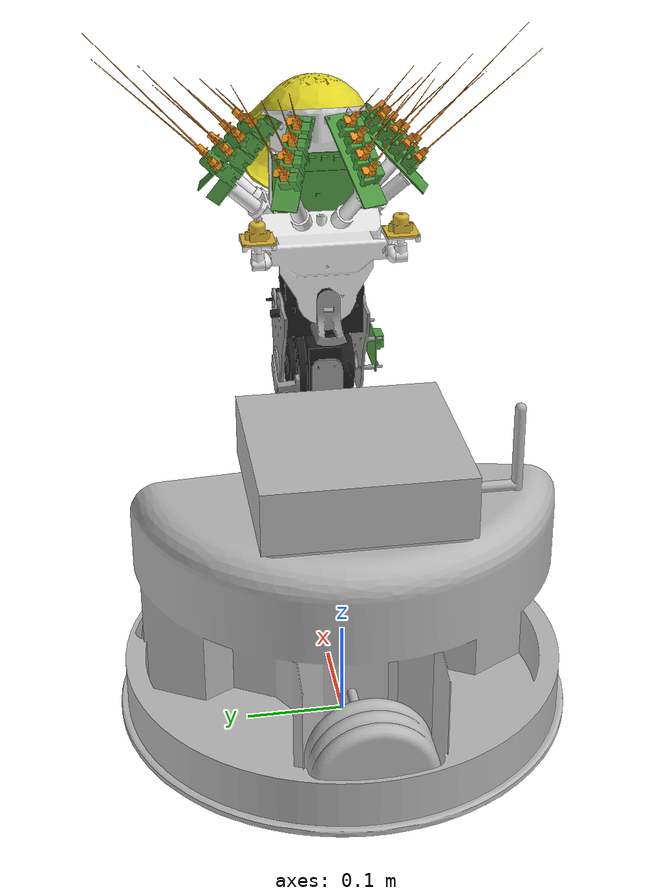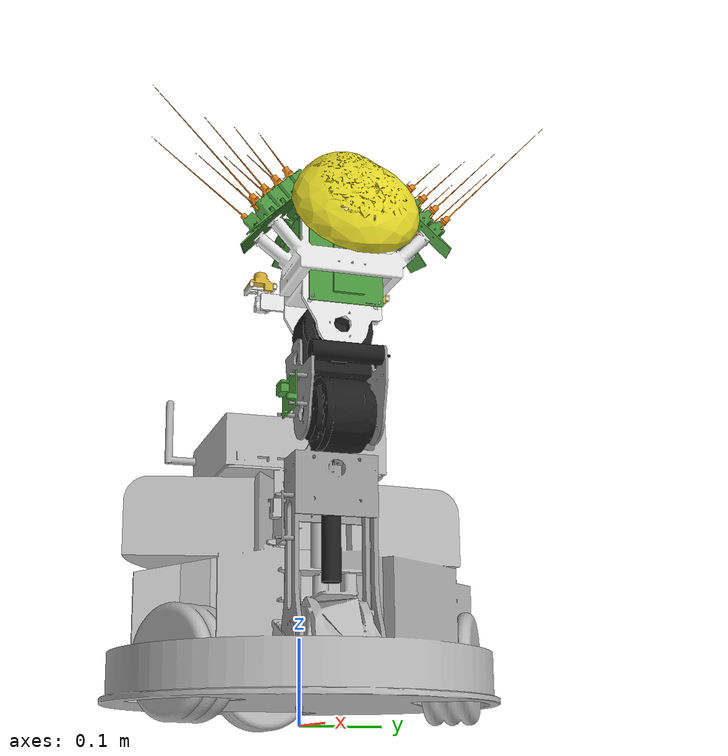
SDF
<?xml version="1.0"?>
<sdf version="1.5">
	<model name="whiskeye_robot">

		<link name="body">
			<inertial>
				<pose>0 0 0.1 0 0 0</pose>
				<mass>10.0</mass>
				<inertia>
					<ixx>1.0</ixx>
					<ixy>0</ixy>
					<ixz>0</ixz>
					<iyy>1.0</iyy>
					<iyz>0</iyz>
					<izz>1.0</izz>
				</inertia>
			</inertial>
			<visual name="whiskeye_body-3_rl-d-30-101-50-01033_complete-1.dae_visual">
				<pose>0 0 0 0 0 0</pose>
				<geometry>
					<mesh>
						<uri>model://whiskeye_robot/mesh/hi/whiskeye_body-3_rl-d-30-101-50-01033_complete-1.dae</uri>
					</mesh>
				</geometry>
			</visual>

			<visual name="whiskeye_body-3_host_pc-1.dae_visual">
				<pose>0 0 0 0 0 0</pose>
				<geometry>
					<mesh>
						<uri>model://whiskeye_robot/mesh/hi/whiskeye_body-3_host_pc-1.dae</uri>
					</mesh>
				</geometry>

			</visual>

			<visual name="whiskeye_body-3_ec-22_large-1.dae_visual">
				<pose>0 0 0 0 0 0</pose>
				<geometry>
					<mesh>
						<uri>model://whiskeye_robot/mesh/hi/whiskeye_body-3_ec-22_large-1.dae</uri>
					</mesh>
				</geometry>
			</visual>

			<visual name="whiskeye_body-3_wheel-1.dae_visual">
				<pose>0 0 0 0 0 0</pose>
				<geometry>
					<mesh>
						<uri>model://whiskeye_robot/mesh/hi/whiskeye_body-3_wheel-1.dae</uri>
					</mesh>
				</geometry>
			</visual>

			<visual name="whiskeye_body-3_wheel-3.dae_visual">
				<pose>0 0 0 0 0 0</pose>
				<geometry>
					<mesh>
						<uri>model://whiskeye_robot/mesh/hi/whiskeye_body-3_wheel-3.dae</uri>
					</mesh>
				</geometry>
			</visual>

			<visual name="whiskeye_body-3_body-1.dae_visual">
				<pose>0 0 0 0 0 0</pose>
				<geometry>
					<mesh>
						<uri>model://whiskeye_robot/mesh/hi/whiskeye_body-3_body-1.dae</uri>
					</mesh>
				</geometry>
			</visual>

			<visual name="whiskeye_body-3_myomotordriverpcb-1.dae_visual">
				<pose>0 0 0 0 0 0</pose>
				<geometry>
					<mesh>
						<uri>model://whiskeye_robot/mesh/hi/whiskeye_body-3_myomotordriverpcb-1.dae</uri>
					</mesh>
				</geometry>
			</visual>

			<visual name="whiskeye_body-3_wheel-2.dae_visual">
				<pose>0 0 0 0 0 0</pose>
				<geometry>
					<mesh>
						<uri>model://whiskeye_robot/mesh/hi/whiskeye_body-3_wheel-2.dae</uri>
					</mesh>
				</geometry>
			</visual>

			<collision name="whiskeye_body-3_rl-d-30-101-50-01033_complete-1.dae_collision">
				<pose>0 0 0 0 0 0</pose>
				<geometry>
					<mesh>
						<uri>model://whiskeye_robot/mesh/lo/whiskeye_body-3_rl-d-30-101-50-01033_complete-1.dae</uri>
					</mesh>
				</geometry>
				<surface>
					<friction>
						<ode>
							<mu>0.1</mu>
							<mu2>0.1</mu2>
						</ode>
					</friction>
				</surface>
			</collision>

			<collision name="whiskeye_body-3_host_pc-1.dae_collision">
				<pose>0 0 0 0 0 0</pose>
				<geometry>
					<mesh>
						<uri>model://whiskeye_robot/mesh/lo/whiskeye_body-3_host_pc-1.dae</uri>
					</mesh>
				</geometry>
				<surface>
					<friction>
						<ode>
							<mu>0.1</mu>
							<mu2>0.1</mu2>
						</ode>
					</friction>
				</surface>
			</collision>

			<collision name="whiskeye_body-3_ec-22_large-1.dae_collision">
				<pose>0 0 0 0 0 0</pose>
				<geometry>
					<mesh>
						<uri>model://whiskeye_robot/mesh/lo/whiskeye_body-3_ec-22_large-1.dae</uri>
					</mesh>
				</geometry>
				<surface>
					<friction>
						<ode>
							<mu>0.1</mu>
							<mu2>0.1</mu2>
						</ode>
					</friction>
				</surface>
			</collision>

			<collision name="whiskeye_body-3_wheel-1.dae_collision">
				<pose>0 0 0 0 0 0</pose>
				<geometry>
					<mesh>
						<uri>model://whiskeye_robot/mesh/lo/whiskeye_body-3_wheel-1.dae</uri>
					</mesh>
				</geometry>
				<surface>
					<friction>
						<ode>
							<mu>0.1</mu>
							<mu2>0.1</mu2>
						</ode>
					</friction>
				</surface>
			</collision>

			<collision name="whiskeye_body-3_wheel-3.dae_collision">
				<pose>0 0 0 0 0 0</pose>
				<geometry>
					<mesh>
						<uri>model://whiskeye_robot/mesh/lo/whiskeye_body-3_wheel-3.dae</uri>
					</mesh>
				</geometry>
				<surface>
					<friction>
						<ode>
							<mu>0.1</mu>
							<mu2>0.1</mu2>
						</ode>
					</friction>
				</surface>
			</collision>

			<collision name="whiskeye_body-3_body-1.dae_collision">
				<pose>0 0 0 0 0 0</pose>
				<geometry>
					<mesh>
						<uri>model://whiskeye_robot/mesh/lo/whiskeye_body-3_body-1.dae</uri>
					</mesh>
				</geometry>
				<surface>
					<friction>
						<ode>
							<mu>0.1</mu>
							<mu2>0.1</mu2>
						</ode>
					</friction>
				</surface>
			</collision>

			<collision name="whiskeye_body-3_myomotordriverpcb-1.dae_collision">
				<pose>0 0 0 0 0 0</pose>
				<geometry>
					<mesh>
						<uri>model://whiskeye_robot/mesh/lo/whiskeye_body-3_myomotordriverpcb-1.dae</uri>
					</mesh>
				</geometry>
				<surface>
					<friction>
						<ode>
							<mu>0.1</mu>
							<mu2>0.1</mu2>
						</ode>
					</friction>
				</surface>
			</collision>

			<collision name="whiskeye_body-3_wheel-2.dae_collision">
				<pose>0 0 0 0 0 0</pose>
				<geometry>
					<mesh>
						<uri>model://whiskeye_robot/mesh/lo/whiskeye_body-3_wheel-2.dae</uri>
					</mesh>
				</geometry>
				<surface>
					<friction>
						<ode>
							<mu>0.1</mu>
							<mu2>0.1</mu2>
						</ode>
					</friction>
				</surface>
			</collision>

			<sensor name="imu_body" type="imu">
				<pose>0 0 0 0 0 0</pose>
				<always_on>1</always_on>
				<update_rate>50</update_rate>
				<visualize>false</visualize>
			</sensor>

		</link>

		<joint type="revolute" name="body_neck">
			<pose>0.128651992798 -7.90977478027e-06 0.0798500061035 0 0 0</pose>
			<parent>body</parent>
			<child>neck</child>
			<axis>
				<xyz>0.0 0.001 0.0</xyz>
				<limit>
					<lower>0.0</lower>
					<upper>1.2217304763960306</upper>
				</limit>
				<dynamics>
					<friction>0.5</friction>
					<damping>0.5</damping>
				</dynamics>
			</axis>
		</joint>

		<link name="neck">
			<inertial>
				<pose>0.144151977539 -8.86344909668e-06 0.203515487671 0 0 0</pose>
				<mass>0.5</mass>
				<inertia>
					<ixx>0.05</ixx>
					<ixy>0</ixy>
					<ixz>0</ixz>
					<iyy>0.05</iyy>
					<iyz>0</iyz>
					<izz>0.05</izz>
				</inertia>
			</inertial>
			<visual name="whiskeye_neck-2_rl-d-20-101-38-01033_complete-1.dae_visual">
				<pose>0 0 0 0 0 0</pose>
				<geometry>
					<mesh>
						<uri>model://whiskeye_robot/mesh/hi/whiskeye_neck-2_rl-d-20-101-38-01033_complete-1.dae</uri>
					</mesh>
				</geometry>
				<material>
					<script>
						<uri>file://media/materials/scripts/gazebo.material</uri>
						<name>Gazebo/FlatBlack</name>
					</script>
				</material>
			</visual>

			<visual name="whiskeye_neck-2_neck-1.dae_visual">
				<pose>0 0 0 0 0 0</pose>
				<geometry>
					<mesh>
						<uri>model://whiskeye_robot/mesh/hi/whiskeye_neck-2_neck-1.dae</uri>
					</mesh>
				</geometry>
				<material>
					<script>
						<uri>file://media/materials/scripts/gazebo.material</uri>
						<name>Gazebo/Grey</name>
					</script>
				</material>
			</visual>

			<visual name="whiskeye_neck-2_myomotordriverpcb-1.dae_visual">
				<pose>0 0 0 0 0 0</pose>
				<geometry>
					<mesh>
						<uri>model://whiskeye_robot/mesh/hi/whiskeye_neck-2_myomotordriverpcb-1.dae</uri>
					</mesh>
				</geometry>

			</visual>

			<visual name="whiskeye_neck-2_ec-22_large-1.dae_visual">
				<pose>0 0 0 0 0 0</pose>
				<geometry>
					<mesh>
						<uri>model://whiskeye_robot/mesh/hi/whiskeye_neck-2_ec-22_large-1.dae</uri>
					</mesh>
				</geometry>
				<material>
					<script>
						<uri>file://media/materials/scripts/gazebo.material</uri>
						<name>Gazebo/FlatBlack</name>
					</script>
				</material>
			</visual>

			<collision name="whiskeye_neck-2_rl-d-20-101-38-01033_complete-1.dae_collision">
				<pose>0 0 0 0 0 0</pose>
				<geometry>
					<mesh>
						<uri>model://whiskeye_robot/mesh/lo/whiskeye_neck-2_rl-d-20-101-38-01033_complete-1.dae</uri>
					</mesh>
				</geometry>
				<surface>
					<friction>
						<ode>
							<mu>0.1</mu>
							<mu2>0.1</mu2>
						</ode>
					</friction>
				</surface>
			</collision>

			<collision name="whiskeye_neck-2_neck-1.dae_collision">
				<pose>0 0 0 0 0 0</pose>
				<geometry>
					<mesh>
						<uri>model://whiskeye_robot/mesh/lo/whiskeye_neck-2_neck-1.dae</uri>
					</mesh>
				</geometry>
				<surface>
					<friction>
						<ode>
							<mu>0.1</mu>
							<mu2>0.1</mu2>
						</ode>
					</friction>
				</surface>
			</collision>

			<collision name="whiskeye_neck-2_myomotordriverpcb-1.dae_collision">
				<pose>0 0 0 0 0 0</pose>
				<geometry>
					<mesh>
						<uri>model://whiskeye_robot/mesh/lo/whiskeye_neck-2_myomotordriverpcb-1.dae</uri>
					</mesh>
				</geometry>
				<surface>
					<friction>
						<ode>
							<mu>0.1</mu>
							<mu2>0.1</mu2>
						</ode>
					</friction>
				</surface>
			</collision>

			<collision name="whiskeye_neck-2_ec-22_large-1.dae_collision">
				<pose>0 0 0 0 0 0</pose>
				<geometry>
					<mesh>
						<uri>model://whiskeye_robot/mesh/lo/whiskeye_neck-2_ec-22_large-1.dae</uri>
					</mesh>
				</geometry>
				<surface>
					<friction>
						<ode>
							<mu>0.1</mu>
							<mu2>0.1</mu2>
						</ode>
					</friction>
				</surface>
			</collision>

		</link>

		<joint type="revolute" name="neck_gmbl">
			<pose>0.159651977539 -9.81712341309e-06 0.327180969238 0 0 0</pose>
			<parent>neck</parent>
			<child>gmbl</child>
			<axis>
				<xyz>0.0 0.001 0.0</xyz>
				<limit>
					<lower>0.0</lower>
					<upper>2.0943951023931953</upper>
				</limit>
				<dynamics>
					<friction>0.5</friction>
					<damping>0.5</damping>
				</dynamics>
			</axis>
		</joint>

		<link name="gmbl">
			<inertial>
				<pose>0.148526977539 -0.000217275589705 0.377305969238 0 0 0</pose>
				<mass>0.25</mass>
				<inertia>
					<ixx>0.025</ixx>
					<ixy>0</ixy>
					<ixz>0</ixz>
					<iyy>0.025</iyy>
					<iyz>0</iyz>
					<izz>0.025</izz>
				</inertia>
			</inertial>
			<visual name="whiskeye_gimbal-1_myomotordriverpcb-2.dae_visual">
				<pose>0 0 0 0 0 0</pose>
				<geometry>
					<mesh>
						<uri>model://whiskeye_robot/mesh/hi/whiskeye_gimbal-1_myomotordriverpcb-2.dae</uri>
					</mesh>
				</geometry>
				<material>
					<script>
						<uri>file://media/materials/scripts/gazebo.material</uri>
						<name>Gazebo/Grass</name>
					</script>
				</material>
			</visual>

			<visual name="whiskeye_gimbal-1_ec-22_medium-2.dae_visual">
				<pose>0 0 0 0 0 0</pose>
				<geometry>
					<mesh>
						<uri>model://whiskeye_robot/mesh/hi/whiskeye_gimbal-1_ec-22_medium-2.dae</uri>
					</mesh>
				</geometry>
				<material>
					<script>
						<uri>file://media/materials/scripts/gazebo.material</uri>
						<name>Gazebo/FlatBlack</name>
					</script>
				</material>
			</visual>

			<visual name="whiskeye_gimbal-1_rl-d-20-101-38-01033_complete-1.dae_visual">
				<pose>0 0 0 0 0 0</pose>
				<geometry>
					<mesh>
						<uri>model://whiskeye_robot/mesh/hi/whiskeye_gimbal-1_rl-d-20-101-38-01033_complete-1.dae</uri>
					</mesh>
				</geometry>
				<material>
					<script>
						<uri>file://media/materials/scripts/gazebo.material</uri>
						<name>Gazebo/FlatBlack</name>
					</script>
				</material>
			</visual>

			<visual name="whiskeye_gimbal-1_gimbal_frame-1.dae_visual">
				<pose>0 0 0 0 0 0</pose>
				<geometry>
					<mesh>
						<uri>model://whiskeye_robot/mesh/hi/whiskeye_gimbal-1_gimbal_frame-1.dae</uri>
					</mesh>
				</geometry>
				<material>
					<script>
						<uri>file://media/materials/scripts/gazebo.material</uri>
						<name>Gazebo/Grey</name>
					</script>
				</material>
			</visual>

			<collision name="whiskeye_gimbal-1_myomotordriverpcb-2.dae_collision">
				<pose>0 0 0 0 0 0</pose>
				<geometry>
					<mesh>
						<uri>model://whiskeye_robot/mesh/lo/whiskeye_gimbal-1_myomotordriverpcb-2.dae</uri>
					</mesh>
				</geometry>
				<surface>
					<friction>
						<ode>
							<mu>0.1</mu>
							<mu2>0.1</mu2>
						</ode>
					</friction>
				</surface>
			</collision>

			<collision name="whiskeye_gimbal-1_ec-22_medium-2.dae_collision">
				<pose>0 0 0 0 0 0</pose>
				<geometry>
					<mesh>
						<uri>model://whiskeye_robot/mesh/lo/whiskeye_gimbal-1_ec-22_medium-2.dae</uri>
					</mesh>
				</geometry>
				<surface>
					<friction>
						<ode>
							<mu>0.1</mu>
							<mu2>0.1</mu2>
						</ode>
					</friction>
				</surface>
			</collision>

			<collision name="whiskeye_gimbal-1_rl-d-20-101-38-01033_complete-1.dae_collision">
				<pose>0 0 0 0 0 0</pose>
				<geometry>
					<mesh>
						<uri>model://whiskeye_robot/mesh/lo/whiskeye_gimbal-1_rl-d-20-101-38-01033_complete-1.dae</uri>
					</mesh>
				</geometry>
				<surface>
					<friction>
						<ode>
							<mu>0.1</mu>
							<mu2>0.1</mu2>
						</ode>
					</friction>
				</surface>
			</collision>

			<collision name="whiskeye_gimbal-1_gimbal_frame-1.dae_collision">
				<pose>0 0 0 0 0 0</pose>
				<geometry>
					<mesh>
						<uri>model://whiskeye_robot/mesh/lo/whiskeye_gimbal-1_gimbal_frame-1.dae</uri>
					</mesh>
				</geometry>
				<surface>
					<friction>
						<ode>
							<mu>0.1</mu>
							<mu2>0.1</mu2>
						</ode>
					</friction>
				</surface>
			</collision>

		</link>

		<joint type="revolute" name="gmbl_head">
			<pose>0.137401992798 -0.000424734055996 0.427430999756 0 0 0</pose>
			<parent>gmbl</parent>
			<child>head</child>
			<axis>
				<xyz>-0.001 0.0 0.0</xyz>
				<limit>
					<lower>-1.5707963267948966</lower>
					<upper>1.5707963267948966</upper>
				</limit>
				<dynamics>
					<friction>0.5</friction>
					<damping>0.5</damping>
				</dynamics>
			</axis>
		</joint>

		<link name="head">
			<inertial>
				<pose>0.137401992798 -0.000424734055996 0.527430999756 0 0 0</pose>
				<mass>0.5</mass>
				<inertia>
					<ixx>0.05</ixx>
					<ixy>0</ixy>
					<ixz>0</ixz>
					<iyy>0.05</iyy>
					<iyz>0</iyz>
					<izz>0.05</izz>
				</inertia>
			</inertial>
			<visual name="whiskeye_head-1_row_mini-4_row_reduced-1.dae_visual">
				<pose>0 0 0 0 0 0</pose>
				<geometry>
					<mesh>
						<uri>model://whiskeye_robot/mesh/hi/whiskeye_head-1_row_mini-4_row_reduced-1.dae</uri>
					</mesh>
				</geometry>
				<material>
					<script>
						<uri>file://media/materials/scripts/gazebo.material</uri>
						<name>Gazebo/Grass</name>
					</script>
				</material>
			</visual>

			<visual name="whiskeye_head-1_row_mini-5_row_reduced-1.dae_visual">
				<pose>0 0 0 0 0 0</pose>
				<geometry>
					<mesh>
						<uri>model://whiskeye_robot/mesh/hi/whiskeye_head-1_row_mini-5_row_reduced-1.dae</uri>
					</mesh>
				</geometry>
				<material>
					<script>
						<uri>file://media/materials/scripts/gazebo.material</uri>
						<name>Gazebo/Grass</name>
					</script>
				</material>
			</visual>

			<visual name="whiskeye_head-1_pearnana_tangoblack-1.dae_visual">
				<pose>0 0 0 0 0 0</pose>
				<geometry>
					<mesh>
						<uri>model://whiskeye_robot/mesh/hi/whiskeye_head-1_pearnana_tangoblack-1.dae</uri>
					</mesh>
				</geometry>
				<material>
					<script>
						<uri>file://media/materials/scripts/gazebo.material</uri>
						<name>Gazebo/DarkYellow</name>
					</script>
				</material>
			</visual>

			<visual name="whiskeye_head-1_elp_camera-2.dae_visual">
				<pose>0 0 0 0 0 0</pose>
				<geometry>
					<mesh>
						<uri>model://whiskeye_robot/mesh/hi/whiskeye_head-1_elp_camera-2.dae</uri>
					</mesh>
				</geometry>
				<material>
					<script>
						<uri>file://media/materials/scripts/gazebo.material</uri>
						<name>Gazebo/Gold</name>
					</script>
				</material>
			</visual>

			<visual name="whiskeye_head-1_eyemount_yaw-4.dae_visual">
				<pose>0 0 0 0 0 0</pose>
				<geometry>
					<mesh>
						<uri>model://whiskeye_robot/mesh/hi/whiskeye_head-1_eyemount_yaw-4.dae</uri>
					</mesh>
				</geometry>
				<material>
					<script>
						<uri>file://media/materials/scripts/gazebo.material</uri>
						<name>Gazebo/White</name>
					</script>
				</material>
			</visual>

			<visual name="whiskeye_head-1_elp_camera-1.dae_visual">
				<pose>0 0 0 0 0 0</pose>
				<geometry>
					<mesh>
						<uri>model://whiskeye_robot/mesh/hi/whiskeye_head-1_elp_camera-1.dae</uri>
					</mesh>
				</geometry>
				<material>
					<script>
						<uri>file://media/materials/scripts/gazebo.material</uri>
						<name>Gazebo/Gold</name>
					</script>
				</material>
			</visual>

			<visual name="whiskeye_head-1_eyemount_camholder_reduced-2.dae_visual">
				<pose>0 0 0 0 0 0</pose>
				<geometry>
					<mesh>
						<uri>model://whiskeye_robot/mesh/hi/whiskeye_head-1_eyemount_camholder_reduced-2.dae</uri>
					</mesh>
				</geometry>
				<material>
					<script>
						<uri>file://media/materials/scripts/gazebo.material</uri>
						<name>Gazebo/White</name>
					</script>
				</material>
			</visual>

			<visual name="whiskeye_head-1_row_mini-3_row_reduced-1.dae_visual">
				<pose>0 0 0 0 0 0</pose>
				<geometry>
					<mesh>
						<uri>model://whiskeye_robot/mesh/hi/whiskeye_head-1_row_mini-3_row_reduced-1.dae</uri>
					</mesh>
				</geometry>
				<material>
					<script>
						<uri>file://media/materials/scripts/gazebo.material</uri>
						<name>Gazebo/Grass</name>
					</script>
				</material>
			</visual>

			<visual name="whiskeye_head-1_row_mini-2_row_reduced-1.dae_visual">
				<pose>0 0 0 0 0 0</pose>
				<geometry>
					<mesh>
						<uri>model://whiskeye_robot/mesh/hi/whiskeye_head-1_row_mini-2_row_reduced-1.dae</uri>
					</mesh>
				</geometry>
				<material>
					<script>
						<uri>file://media/materials/scripts/gazebo.material</uri>
						<name>Gazebo/Grass</name>
					</script>
				</material>
			</visual>

			<visual name="whiskeye_head-1_eyemount_yaw-3.dae_visual">
				<pose>0 0 0 0 0 0</pose>
				<geometry>
					<mesh>
						<uri>model://whiskeye_robot/mesh/hi/whiskeye_head-1_eyemount_yaw-3.dae</uri>
					</mesh>
				</geometry>
				<material>
					<script>
						<uri>file://media/materials/scripts/gazebo.material</uri>
						<name>Gazebo/White</name>
					</script>
				</material>
			</visual>

			<visual name="whiskeye_head-1_eyemount_camholder_reduced-1.dae_visual">
				<pose>0 0 0 0 0 0</pose>
				<geometry>
					<mesh>
						<uri>model://whiskeye_robot/mesh/hi/whiskeye_head-1_eyemount_camholder_reduced-1.dae</uri>
					</mesh>
				</geometry>
				<material>
					<script>
						<uri>file://media/materials/scripts/gazebo.material</uri>
						<name>Gazebo/White</name>
					</script>
				</material>
			</visual>

			<visual name="whiskeye_head-1_pi_compute-1.dae_visual">
				<pose>0 0 0 0 0 0</pose>
				<geometry>
					<mesh>
						<uri>model://whiskeye_robot/mesh/hi/whiskeye_head-1_pi_compute-1.dae</uri>
					</mesh>
				</geometry>
				<material>
					<script>
						<uri>file://media/materials/scripts/gazebo.material</uri>
						<name>Gazebo/Grass</name>
					</script>
				</material>
			</visual>

			<visual name="whiskeye_head-1_head_barebones-1.dae_visual">
				<pose>0 0 0 0 0 0</pose>
				<geometry>
					<mesh>
						<uri>model://whiskeye_robot/mesh/hi/whiskeye_head-1_head_barebones-1.dae</uri>
					</mesh>
				</geometry>
				<material>
					<script>
						<uri>file://media/materials/scripts/gazebo.material</uri>
						<name>Gazebo/White</name>
					</script>
				</material>
			</visual>

			<visual name="whiskeye_head-1_eyemount_elevation-1.dae_visual">
				<pose>0 0 0 0 0 0</pose>
				<geometry>
					<mesh>
						<uri>model://whiskeye_robot/mesh/hi/whiskeye_head-1_eyemount_elevation-1.dae</uri>
					</mesh>
				</geometry>
				<material>
					<script>
						<uri>file://media/materials/scripts/gazebo.material</uri>
						<name>Gazebo/White</name>
					</script>
				</material>
			</visual>

			<visual name="whiskeye_head-1_row_mini-1_row_reduced-1.dae_visual">
				<pose>0 0 0 0 0 0</pose>
				<geometry>
					<mesh>
						<uri>model://whiskeye_robot/mesh/hi/whiskeye_head-1_row_mini-1_row_reduced-1.dae</uri>
					</mesh>
				</geometry>
				<material>
					<script>
						<uri>file://media/materials/scripts/gazebo.material</uri>
						<name>Gazebo/Grass</name>
					</script>
				</material>
			</visual>

			<visual name="whiskeye_head-1_row_mini-6_row_reduced-1.dae_visual">
				<pose>0 0 0 0 0 0</pose>
				<geometry>
					<mesh>
						<uri>model://whiskeye_robot/mesh/hi/whiskeye_head-1_row_mini-6_row_reduced-1.dae</uri>
					</mesh>
				</geometry>
				<material>
					<script>
						<uri>file://media/materials/scripts/gazebo.material</uri>
						<name>Gazebo/Grass</name>
					</script>
				</material>
			</visual>

			<visual name="whiskeye_head-1_pcb_head-1.dae_visual">
				<pose>0 0 0 0 0 0</pose>
				<geometry>
					<mesh>
						<uri>model://whiskeye_robot/mesh/hi/whiskeye_head-1_pcb_head-1.dae</uri>
					</mesh>
				</geometry>
				<material>
					<script>
						<uri>file://media/materials/scripts/gazebo.material</uri>
						<name>Gazebo/Grass</name>
					</script>
				</material>
			</visual>

			<visual name="whiskeye_head-1_eyemount_elevation-2.dae_visual">
				<pose>0 0 0 0 0 0</pose>
				<geometry>
					<mesh>
						<uri>model://whiskeye_robot/mesh/hi/whiskeye_head-1_eyemount_elevation-2.dae</uri>
					</mesh>
				</geometry>
				<material>
					<script>
						<uri>file://media/materials/scripts/gazebo.material</uri>
						<name>Gazebo/White</name>
					</script>
				</material>
			</visual>

			<collision name="whiskeye_head-1_row_mini-4_row_reduced-1.dae_collision">
				<pose>0 0 0 0 0 0</pose>
				<geometry>
					<mesh>
						<uri>model://whiskeye_robot/mesh/lo/whiskeye_head-1_row_mini-4_row_reduced-1.dae</uri>
					</mesh>
				</geometry>
				<surface>
					<friction>
						<ode>
							<mu>0.1</mu>
							<mu2>0.1</mu2>
						</ode>
					</friction>
				</surface>
			</collision>

			<collision name="whiskeye_head-1_row_mini-5_row_reduced-1.dae_collision">
				<pose>0 0 0 0 0 0</pose>
				<geometry>
					<mesh>
						<uri>model://whiskeye_robot/mesh/lo/whiskeye_head-1_row_mini-5_row_reduced-1.dae</uri>
					</mesh>
				</geometry>
				<surface>
					<friction>
						<ode>
							<mu>0.1</mu>
							<mu2>0.1</mu2>
						</ode>
					</friction>
				</surface>
			</collision>

			<collision name="whiskeye_head-1_pearnana_tangoblack-1.dae_collision">
				<pose>0 0 0 0 0 0</pose>
				<geometry>
					<mesh>
						<uri>model://whiskeye_robot/mesh/lo/whiskeye_head-1_pearnana_tangoblack-1.dae</uri>
					</mesh>
				</geometry>
				<surface>
					<friction>
						<ode>
							<mu>0.1</mu>
							<mu2>0.1</mu2>
						</ode>
					</friction>
				</surface>
			</collision>

			<collision name="whiskeye_head-1_elp_camera-2.dae_collision">
				<pose>0 0 0 0 0 0</pose>
				<geometry>
					<mesh>
						<uri>model://whiskeye_robot/mesh/lo/whiskeye_head-1_elp_camera-2.dae</uri>
					</mesh>
				</geometry>
				<surface>
					<friction>
						<ode>
							<mu>0.1</mu>
							<mu2>0.1</mu2>
						</ode>
					</friction>
				</surface>
			</collision>

			<collision name="whiskeye_head-1_eyemount_yaw-4.dae_collision">
				<pose>0 0 0 0 0 0</pose>
				<geometry>
					<mesh>
						<uri>model://whiskeye_robot/mesh/lo/whiskeye_head-1_eyemount_yaw-4.dae</uri>
					</mesh>
				</geometry>
				<surface>
					<friction>
						<ode>
							<mu>0.1</mu>
							<mu2>0.1</mu2>
						</ode>
					</friction>
				</surface>
			</collision>

			<collision name="whiskeye_head-1_elp_camera-1.dae_collision">
				<pose>0 0 0 0 0 0</pose>
				<geometry>
					<mesh>
						<uri>model://whiskeye_robot/mesh/lo/whiskeye_head-1_elp_camera-1.dae</uri>
					</mesh>
				</geometry>
				<surface>
					<friction>
						<ode>
							<mu>0.1</mu>
							<mu2>0.1</mu2>
						</ode>
					</friction>
				</surface>
			</collision>

			<collision name="whiskeye_head-1_eyemount_camholder_reduced-2.dae_collision">
				<pose>0 0 0 0 0 0</pose>
				<geometry>
					<mesh>
						<uri>model://whiskeye_robot/mesh/lo/whiskeye_head-1_eyemount_camholder_reduced-2.dae</uri>
					</mesh>
				</geometry>
				<surface>
					<friction>
						<ode>
							<mu>0.1</mu>
							<mu2>0.1</mu2>
						</ode>
					</friction>
				</surface>
			</collision>

			<collision name="whiskeye_head-1_row_mini-3_row_reduced-1.dae_collision">
				<pose>0 0 0 0 0 0</pose>
				<geometry>
					<mesh>
						<uri>model://whiskeye_robot/mesh/lo/whiskeye_head-1_row_mini-3_row_reduced-1.dae</uri>
					</mesh>
				</geometry>
				<surface>
					<friction>
						<ode>
							<mu>0.1</mu>
							<mu2>0.1</mu2>
						</ode>
					</friction>
				</surface>
			</collision>

			<collision name="whiskeye_head-1_row_mini-2_row_reduced-1.dae_collision">
				<pose>0 0 0 0 0 0</pose>
				<geometry>
					<mesh>
						<uri>model://whiskeye_robot/mesh/lo/whiskeye_head-1_row_mini-2_row_reduced-1.dae</uri>
					</mesh>
				</geometry>
				<surface>
					<friction>
						<ode>
							<mu>0.1</mu>
							<mu2>0.1</mu2>
						</ode>
					</friction>
				</surface>
			</collision>

			<collision name="whiskeye_head-1_eyemount_yaw-3.dae_collision">
				<pose>0 0 0 0 0 0</pose>
				<geometry>
					<mesh>
						<uri>model://whiskeye_robot/mesh/lo/whiskeye_head-1_eyemount_yaw-3.dae</uri>
					</mesh>
				</geometry>
				<surface>
					<friction>
						<ode>
							<mu>0.1</mu>
							<mu2>0.1</mu2>
						</ode>
					</friction>
				</surface>
			</collision>

			<collision name="whiskeye_head-1_eyemount_camholder_reduced-1.dae_collision">
				<pose>0 0 0 0 0 0</pose>
				<geometry>
					<mesh>
						<uri>model://whiskeye_robot/mesh/lo/whiskeye_head-1_eyemount_camholder_reduced-1.dae</uri>
					</mesh>
				</geometry>
				<surface>
					<friction>
						<ode>
							<mu>0.1</mu>
							<mu2>0.1</mu2>
						</ode>
					</friction>
				</surface>
			</collision>

			<collision name="whiskeye_head-1_pi_compute-1.dae_collision">
				<pose>0 0 0 0 0 0</pose>
				<geometry>
					<mesh>
						<uri>model://whiskeye_robot/mesh/lo/whiskeye_head-1_pi_compute-1.dae</uri>
					</mesh>
				</geometry>
				<surface>
					<friction>
						<ode>
							<mu>0.1</mu>
							<mu2>0.1</mu2>
						</ode>
					</friction>
				</surface>
			</collision>

			<collision name="whiskeye_head-1_head_barebones-1.dae_collision">
				<pose>0 0 0 0 0 0</pose>
				<geometry>
					<mesh>
						<uri>model://whiskeye_robot/mesh/lo/whiskeye_head-1_head_barebones-1.dae</uri>
					</mesh>
				</geometry>
				<surface>
					<friction>
						<ode>
							<mu>0.1</mu>
							<mu2>0.1</mu2>
						</ode>
					</friction>
				</surface>
			</collision>

			<collision name="whiskeye_head-1_eyemount_elevation-1.dae_collision">
				<pose>0 0 0 0 0 0</pose>
				<geometry>
					<mesh>
						<uri>model://whiskeye_robot/mesh/lo/whiskeye_head-1_eyemount_elevation-1.dae</uri>
					</mesh>
				</geometry>
				<surface>
					<friction>
						<ode>
							<mu>0.1</mu>
							<mu2>0.1</mu2>
						</ode>
					</friction>
				</surface>
			</collision>

			<collision name="whiskeye_head-1_row_mini-1_row_reduced-1.dae_collision">
				<pose>0 0 0 0 0 0</pose>
				<geometry>
					<mesh>
						<uri>model://whiskeye_robot/mesh/lo/whiskeye_head-1_row_mini-1_row_reduced-1.dae</uri>
					</mesh>
				</geometry>
				<surface>
					<friction>
						<ode>
							<mu>0.1</mu>
							<mu2>0.1</mu2>
						</ode>
					</friction>
				</surface>
			</collision>

			<collision name="whiskeye_head-1_row_mini-6_row_reduced-1.dae_collision">
				<pose>0 0 0 0 0 0</pose>
				<geometry>
					<mesh>
						<uri>model://whiskeye_robot/mesh/lo/whiskeye_head-1_row_mini-6_row_reduced-1.dae</uri>
					</mesh>
				</geometry>
				<surface>
					<friction>
						<ode>
							<mu>0.1</mu>
							<mu2>0.1</mu2>
						</ode>
					</friction>
				</surface>
			</collision>

			<collision name="whiskeye_head-1_pcb_head-1.dae_collision">
				<pose>0 0 0 0 0 0</pose>
				<geometry>
					<mesh>
						<uri>model://whiskeye_robot/mesh/lo/whiskeye_head-1_pcb_head-1.dae</uri>
					</mesh>
				</geometry>
				<surface>
					<friction>
						<ode>
							<mu>0.1</mu>
							<mu2>0.1</mu2>
						</ode>
					</friction>
				</surface>
			</collision>

			<collision name="whiskeye_head-1_eyemount_elevation-2.dae_collision">
				<pose>0 0 0 0 0 0</pose>
				<geometry>
					<mesh>
						<uri>model://whiskeye_robot/mesh/lo/whiskeye_head-1_eyemount_elevation-2.dae</uri>
					</mesh>
				</geometry>
				<surface>
					<friction>
						<ode>
							<mu>0.1</mu>
							<mu2>0.1</mu2>
						</ode>
					</friction>
				</surface>
			</collision>

			<sensor name="cam0" type="camera">
				<pose>0.0778 0.0573 0.5166 0 -1.5708 0</pose>
				<camera>
					<horizontal_fov>1.57</horizontal_fov>
					<image>
						<width>640</width>
						<height>480</height>
					</image>
					<clip>
						<near>0.001</near>
						<far>100</far>
					</clip>
				</camera>
				<always_on>1</always_on>
				<update_rate>5</update_rate>
				<visualize>false</visualize>
			</sensor>

			<sensor name="cam1" type="camera">
				<pose>0.0778 -0.0573 0.5166 0 -1.5708 0</pose>
				<camera>
					<horizontal_fov>1.57</horizontal_fov>
					<image>
						<width>640</width>
						<height>480</height>
					</image>
					<clip>
						<near>0.001</near>
						<far>100</far>
					</clip>
				</camera>
				<always_on>1</always_on>
				<update_rate>5</update_rate>
				<visualize>false</visualize>
			</sensor>

		</link>

		<joint type="revolute" name="head_whisker1_1">
			<pose>0.204628753662 -0.0665908966064 0.579591186523 0 0 0</pose>
			<parent>head</parent>
			<child>whisker1_1</child>
			<axis>
				<xyz>-0.00097444909811 -0.000218293339014 5.2887044847e-05</xyz>
				<limit>
					<lower>-1.0471975511965976</lower>
					<upper>1.0471975511965976</upper>
				</limit>
				<dynamics>
					<friction>0.1</friction>
					<damping>0.1</damping>
				</dynamics>
			</axis>
		</joint>

		<link name="whisker1_1">
			<inertial>
				<pose>0.204628753662 -0.0665908966064 0.579591186523 0 0 0</pose>
				<mass>0.01</mass>
				<inertia>
					<ixx>0.001</ixx>
					<ixy>0</ixy>
					<ixz>0</ixz>
					<iyy>0.001</iyy>
					<iyz>0</iyz>
					<izz>0.001</izz>
				</inertia>
			</inertial>
			<visual name="whiskeye_head-1_row_mini-1_whiskerasm_50mm-1.dae_visual">
				<pose>0 0 0 0 0 0</pose>
				<geometry>
					<mesh>
						<uri>model://whiskeye_robot/mesh/hi/whiskeye_head-1_row_mini-1_whiskerasm_50mm-1.dae</uri>
					</mesh>
				</geometry>
				<material>
					<script>
						<uri>file://media/materials/scripts/gazebo.material</uri>
						<name>Gazebo/Orange</name>
					</script>
				</material>
			</visual>

			<collision name="whiskeye_head-1_row_mini-1_whiskerasm_50mm-1.dae_collision">
				<pose>0 0 0 0 0 0</pose>
				<geometry>
					<mesh>
						<uri>model://whiskeye_robot/mesh/lo/whiskeye_head-1_row_mini-1_whiskerasm_50mm-1.dae</uri>
					</mesh>
				</geometry>
				<surface>
					<friction>
						<ode>
							<mu>0.1</mu>
							<mu2>0.1</mu2>
						</ode>
					</friction>
				</surface>
			</collision>

			<sensor name="whisker1_1_contact" type="contact">
				<contact>
					<collision>whiskeye_head-1_row_mini-1_whiskerasm_50mm-1.dae_collision</collision>
				</contact>
				<always_on>1</always_on>
				<update_rate>50</update_rate>
				<visualize>false</visualize>
			</sensor>

		</link>

		<joint type="revolute" name="head_whisker1_2">
			<pose>0.206240356445 -0.0794981002808 0.567144165039 0 0 0</pose>
			<parent>head</parent>
			<child>whisker1_2</child>
			<axis>
				<xyz>-0.000982769548893 -0.000183988437057 1.76697019488e-05</xyz>
				<limit>
					<lower>-1.0471975511965976</lower>
					<upper>1.0471975511965976</upper>
				</limit>
				<dynamics>
					<friction>0.1</friction>
					<damping>0.1</damping>
				</dynamics>
			</axis>
		</joint>

		<link name="whisker1_2">
			<inertial>
				<pose>0.206240356445 -0.0794981002808 0.567144165039 0 0 0</pose>
				<mass>0.01</mass>
				<inertia>
					<ixx>0.001</ixx>
					<ixy>0</ixy>
					<ixz>0</ixz>
					<iyy>0.001</iyy>
					<iyz>0</iyz>
					<izz>0.001</izz>
				</inertia>
			</inertial>
			<visual name="whiskeye_head-1_row_mini-1_whiskerasm_70mm-1.dae_visual">
				<pose>0 0 0 0 0 0</pose>
				<geometry>
					<mesh>
						<uri>model://whiskeye_robot/mesh/hi/whiskeye_head-1_row_mini-1_whiskerasm_70mm-1.dae</uri>
					</mesh>
				</geometry>
				<material>
					<script>
						<uri>file://media/materials/scripts/gazebo.material</uri>
						<name>Gazebo/Orange</name>
					</script>
				</material>
			</visual>

			<collision name="whiskeye_head-1_row_mini-1_whiskerasm_70mm-1.dae_collision">
				<pose>0 0 0 0 0 0</pose>
				<geometry>
					<mesh>
						<uri>model://whiskeye_robot/mesh/lo/whiskeye_head-1_row_mini-1_whiskerasm_70mm-1.dae</uri>
					</mesh>
				</geometry>
				<surface>
					<friction>
						<ode>
							<mu>0.1</mu>
							<mu2>0.1</mu2>
						</ode>
					</friction>
				</surface>
			</collision>

			<sensor name="whisker1_2_contact" type="contact">
				<contact>
					<collision>whiskeye_head-1_row_mini-1_whiskerasm_70mm-1.dae_collision</collision>
				</contact>
				<always_on>1</always_on>
				<update_rate>50</update_rate>
				<visualize>false</visualize>
			</sensor>

		</link>

		<joint type="revolute" name="head_whisker1_3">
			<pose>0.207575820923 -0.0920694580078 0.554313964844 0 0 0</pose>
			<parent>head</parent>
			<child>whisker1_3</child>
			<axis>
				<xyz>-0.000988658547401 -0.000149137169123 -1.76757872105e-05</xyz>
				<limit>
					<lower>-1.0471975511965976</lower>
					<upper>1.0471975511965976</upper>
				</limit>
				<dynamics>
					<friction>0.1</friction>
					<damping>0.1</damping>
				</dynamics>
			</axis>
		</joint>

		<link name="whisker1_3">
			<inertial>
				<pose>0.207575820923 -0.0920694580078 0.554313964844 0 0 0</pose>
				<mass>0.01</mass>
				<inertia>
					<ixx>0.001</ixx>
					<ixy>0</ixy>
					<ixz>0</ixz>
					<iyy>0.001</iyy>
					<iyz>0</iyz>
					<izz>0.001</izz>
				</inertia>
			</inertial>
			<visual name="whiskeye_head-1_row_mini-1_whiskerasm_100mm-1.dae_visual">
				<pose>0 0 0 0 0 0</pose>
				<geometry>
					<mesh>
						<uri>model://whiskeye_robot/mesh/hi/whiskeye_head-1_row_mini-1_whiskerasm_100mm-1.dae</uri>
					</mesh>
				</geometry>
				<material>
					<script>
						<uri>file://media/materials/scripts/gazebo.material</uri>
						<name>Gazebo/Orange</name>
					</script>
				</material>
			</visual>

			<collision name="whiskeye_head-1_row_mini-1_whiskerasm_100mm-1.dae_collision">
				<pose>0 0 0 0 0 0</pose>
				<geometry>
					<mesh>
						<uri>model://whiskeye_robot/mesh/lo/whiskeye_head-1_row_mini-1_whiskerasm_100mm-1.dae</uri>
					</mesh>
				</geometry>
				<surface>
					<friction>
						<ode>
							<mu>0.1</mu>
							<mu2>0.1</mu2>
						</ode>
					</friction>
				</surface>
			</collision>

			<sensor name="whisker1_3_contact" type="contact">
				<contact>
					<collision>whiskeye_head-1_row_mini-1_whiskerasm_100mm-1.dae_collision</collision>
				</contact>
				<always_on>1</always_on>
				<update_rate>50</update_rate>
				<visualize>false</visualize>
			</sensor>

		</link>

		<joint type="revolute" name="head_whisker1_4">
			<pose>0.208876739502 -0.10427394104 0.541092468262 0 0 0</pose>
			<parent>head</parent>
			<child>whisker1_4</child>
			<axis>
				<xyz>-0.00099207174778 -0.000114002838731 -5.28868921101e-05</xyz>
				<limit>
					<lower>-1.0471975511965976</lower>
					<upper>1.0471975511965976</upper>
				</limit>
				<dynamics>
					<friction>0.1</friction>
					<damping>0.1</damping>
				</dynamics>
			</axis>
		</joint>

		<link name="whisker1_4">
			<inertial>
				<pose>0.208876739502 -0.10427394104 0.541092468262 0 0 0</pose>
				<mass>0.01</mass>
				<inertia>
					<ixx>0.001</ixx>
					<ixy>0</ixy>
					<ixz>0</ixz>
					<iyy>0.001</iyy>
					<iyz>0</iyz>
					<izz>0.001</izz>
				</inertia>
			</inertial>
			<visual name="whiskeye_head-1_row_mini-1_whiskerasm_160mm-1.dae_visual">
				<pose>0 0 0 0 0 0</pose>
				<geometry>
					<mesh>
						<uri>model://whiskeye_robot/mesh/hi/whiskeye_head-1_row_mini-1_whiskerasm_160mm-1.dae</uri>
					</mesh>
				</geometry>
				<material>
					<script>
						<uri>file://media/materials/scripts/gazebo.material</uri>
						<name>Gazebo/Orange</name>
					</script>
				</material>
			</visual>

			<collision name="whiskeye_head-1_row_mini-1_whiskerasm_160mm-1.dae_collision">
				<pose>0 0 0 0 0 0</pose>
				<geometry>
					<mesh>
						<uri>model://whiskeye_robot/mesh/lo/whiskeye_head-1_row_mini-1_whiskerasm_160mm-1.dae</uri>
					</mesh>
				</geometry>
				<surface>
					<friction>
						<ode>
							<mu>0.1</mu>
							<mu2>0.1</mu2>
						</ode>
					</friction>
				</surface>
			</collision>

			<sensor name="whisker1_4_contact" type="contact">
				<contact>
					<collision>whiskeye_head-1_row_mini-1_whiskerasm_160mm-1.dae_collision</collision>
				</contact>
				<always_on>1</always_on>
				<update_rate>50</update_rate>
				<visualize>false</visualize>
			</sensor>

		</link>

		<joint type="revolute" name="head_whisker2_1">
			<pose>0.157603164673 -0.0624267158508 0.589046142578 0 0 0</pose>
			<parent>head</parent>
			<child>whisker2_1</child>
			<axis>
				<xyz>-0.00094805252552 0.000313686609268 5.28869368136e-05</xyz>
				<limit>
					<lower>-1.0471975511965976</lower>
					<upper>1.0471975511965976</upper>
				</limit>
				<dynamics>
					<friction>0.1</friction>
					<damping>0.1</damping>
				</dynamics>
			</axis>
		</joint>

		<link name="whisker2_1">
			<inertial>
				<pose>0.157603164673 -0.0624267158508 0.589046142578 0 0 0</pose>
				<mass>0.01</mass>
				<inertia>
					<ixx>0.001</ixx>
					<ixy>0</ixy>
					<ixz>0</ixz>
					<iyy>0.001</iyy>
					<iyz>0</iyz>
					<izz>0.001</izz>
				</inertia>
			</inertial>
			<visual name="whiskeye_head-1_row_mini-2_whiskerasm_50mm-1.dae_visual">
				<pose>0 0 0 0 0 0</pose>
				<geometry>
					<mesh>
						<uri>model://whiskeye_robot/mesh/hi/whiskeye_head-1_row_mini-2_whiskerasm_50mm-1.dae</uri>
					</mesh>
				</geometry>
				<material>
					<script>
						<uri>file://media/materials/scripts/gazebo.material</uri>
						<name>Gazebo/Orange</name>
					</script>
				</material>
			</visual>

			<collision name="whiskeye_head-1_row_mini-2_whiskerasm_50mm-1.dae_collision">
				<pose>0 0 0 0 0 0</pose>
				<geometry>
					<mesh>
						<uri>model://whiskeye_robot/mesh/lo/whiskeye_head-1_row_mini-2_whiskerasm_50mm-1.dae</uri>
					</mesh>
				</geometry>
				<surface>
					<friction>
						<ode>
							<mu>0.1</mu>
							<mu2>0.1</mu2>
						</ode>
					</friction>
				</surface>
			</collision>

			<sensor name="whisker2_1_contact" type="contact">
				<contact>
					<collision>whiskeye_head-1_row_mini-2_whiskerasm_50mm-1.dae_collision</collision>
				</contact>
				<always_on>1</always_on>
				<update_rate>50</update_rate>
				<visualize>false</visualize>
			</sensor>

		</link>

		<joint type="revolute" name="head_whisker2_2">
			<pose>0.152350402832 -0.0743263702393 0.576599121094 0 0 0</pose>
			<parent>head</parent>
			<child>whisker2_2</child>
			<axis>
				<xyz>-0.000937554240227 0.000347389727831 1.7675768584e-05</xyz>
				<limit>
					<lower>-1.0471975511965976</lower>
					<upper>1.0471975511965976</upper>
				</limit>
				<dynamics>
					<friction>0.1</friction>
					<damping>0.1</damping>
				</dynamics>
			</axis>
		</joint>

		<link name="whisker2_2">
			<inertial>
				<pose>0.152350402832 -0.0743263702393 0.576599121094 0 0 0</pose>
				<mass>0.01</mass>
				<inertia>
					<ixx>0.001</ixx>
					<ixy>0</ixy>
					<ixz>0</ixz>
					<iyy>0.001</iyy>
					<iyz>0</iyz>
					<izz>0.001</izz>
				</inertia>
			</inertial>
			<visual name="whiskeye_head-1_row_mini-2_whiskerasm_70mm-1.dae_visual">
				<pose>0 0 0 0 0 0</pose>
				<geometry>
					<mesh>
						<uri>model://whiskeye_robot/mesh/hi/whiskeye_head-1_row_mini-2_whiskerasm_70mm-1.dae</uri>
					</mesh>
				</geometry>
				<material>
					<script>
						<uri>file://media/materials/scripts/gazebo.material</uri>
						<name>Gazebo/Orange</name>
					</script>
				</material>
			</visual>

			<collision name="whiskeye_head-1_row_mini-2_whiskerasm_70mm-1.dae_collision">
				<pose>0 0 0 0 0 0</pose>
				<geometry>
					<mesh>
						<uri>model://whiskeye_robot/mesh/lo/whiskeye_head-1_row_mini-2_whiskerasm_70mm-1.dae</uri>
					</mesh>
				</geometry>
				<surface>
					<friction>
						<ode>
							<mu>0.1</mu>
							<mu2>0.1</mu2>
						</ode>
					</friction>
				</surface>
			</collision>

			<sensor name="whisker2_2_contact" type="contact">
				<contact>
					<collision>whiskeye_head-1_row_mini-2_whiskerasm_70mm-1.dae_collision</collision>
				</contact>
				<always_on>1</always_on>
				<update_rate>50</update_rate>
				<visualize>false</visualize>
			</sensor>

		</link>

		<joint type="revolute" name="head_whisker2_3">
			<pose>0.147033416748 -0.0857959899902 0.563768920898 0 0 0</pose>
			<parent>head</parent>
			<child>whisker2_3</child>
			<axis>
				<xyz>-0.000924690067768 0.000380310595036 -1.76697038114e-05</xyz>
				<limit>
					<lower>-1.0471975511965976</lower>
					<upper>1.0471975511965976</upper>
				</limit>
				<dynamics>
					<friction>0.1</friction>
					<damping>0.1</damping>
				</dynamics>
			</axis>
		</joint>

		<link name="whisker2_3">
			<inertial>
				<pose>0.147033416748 -0.0857959899902 0.563768920898 0 0 0</pose>
				<mass>0.01</mass>
				<inertia>
					<ixx>0.001</ixx>
					<ixy>0</ixy>
					<ixz>0</ixz>
					<iyy>0.001</iyy>
					<iyz>0</iyz>
					<izz>0.001</izz>
				</inertia>
			</inertial>
			<visual name="whiskeye_head-1_row_mini-2_whiskerasm_100mm-1.dae_visual">
				<pose>0 0 0 0 0 0</pose>
				<geometry>
					<mesh>
						<uri>model://whiskeye_robot/mesh/hi/whiskeye_head-1_row_mini-2_whiskerasm_100mm-1.dae</uri>
					</mesh>
				</geometry>
				<material>
					<script>
						<uri>file://media/materials/scripts/gazebo.material</uri>
						<name>Gazebo/Orange</name>
					</script>
				</material>
			</visual>

			<collision name="whiskeye_head-1_row_mini-2_whiskerasm_100mm-1.dae_collision">
				<pose>0 0 0 0 0 0</pose>
				<geometry>
					<mesh>
						<uri>model://whiskeye_robot/mesh/lo/whiskeye_head-1_row_mini-2_whiskerasm_100mm-1.dae</uri>
					</mesh>
				</geometry>
				<surface>
					<friction>
						<ode>
							<mu>0.1</mu>
							<mu2>0.1</mu2>
						</ode>
					</friction>
				</surface>
			</collision>

			<sensor name="whisker2_3_contact" type="contact">
				<contact>
					<collision>whiskeye_head-1_row_mini-2_whiskerasm_100mm-1.dae_collision</collision>
				</contact>
				<always_on>1</always_on>
				<update_rate>50</update_rate>
				<visualize>false</visualize>
			</sensor>

		</link>

		<joint type="revolute" name="head_whisker2_4">
			<pose>0.141875396729 -0.0969331665039 0.550547363281 0 0 0</pose>
			<parent>head</parent>
			<child>whisker2_4</child>
			<axis>
				<xyz>-0.000909556686878 0.000412201732397 -5.28808645904e-05</xyz>
				<limit>
					<lower>-1.0471975511965976</lower>
					<upper>1.0471975511965976</upper>
				</limit>
				<dynamics>
					<friction>0.1</friction>
					<damping>0.1</damping>
				</dynamics>
			</axis>
		</joint>

		<link name="whisker2_4">
			<inertial>
				<pose>0.141875396729 -0.0969331665039 0.550547363281 0 0 0</pose>
				<mass>0.01</mass>
				<inertia>
					<ixx>0.001</ixx>
					<ixy>0</ixy>
					<ixz>0</ixz>
					<iyy>0.001</iyy>
					<iyz>0</iyz>
					<izz>0.001</izz>
				</inertia>
			</inertial>
			<visual name="whiskeye_head-1_row_mini-2_whiskerasm_160mm-1.dae_visual">
				<pose>0 0 0 0 0 0</pose>
				<geometry>
					<mesh>
						<uri>model://whiskeye_robot/mesh/hi/whiskeye_head-1_row_mini-2_whiskerasm_160mm-1.dae</uri>
					</mesh>
				</geometry>
				<material>
					<script>
						<uri>file://media/materials/scripts/gazebo.material</uri>
						<name>Gazebo/Orange</name>
					</script>
				</material>
			</visual>

			<collision name="whiskeye_head-1_row_mini-2_whiskerasm_160mm-1.dae_collision">
				<pose>0 0 0 0 0 0</pose>
				<geometry>
					<mesh>
						<uri>model://whiskeye_robot/mesh/lo/whiskeye_head-1_row_mini-2_whiskerasm_160mm-1.dae</uri>
					</mesh>
				</geometry>
				<surface>
					<friction>
						<ode>
							<mu>0.1</mu>
							<mu2>0.1</mu2>
						</ode>
					</friction>
				</surface>
			</collision>

			<sensor name="whisker2_4_contact" type="contact">
				<contact>
					<collision>whiskeye_head-1_row_mini-2_whiskerasm_160mm-1.dae_collision</collision>
				</contact>
				<always_on>1</always_on>
				<update_rate>50</update_rate>
				<visualize>false</visualize>
			</sensor>

		</link>

		<joint type="revolute" name="head_whisker3_1">
			<pose>0.120149620056 -0.0271606674194 0.597895507813 0 0 0</pose>
			<parent>head</parent>
			<child>whisker3_1</child>
			<axis>
				<xyz>-0.000436541616917 0.000898128271103 5.28869479895e-05</xyz>
				<limit>
					<lower>-1.0471975511965976</lower>
					<upper>1.0471975511965976</upper>
				</limit>
				<dynamics>
					<friction>0.1</friction>
					<damping>0.1</damping>
				</dynamics>
			</axis>
		</joint>

		<link name="whisker3_1">
			<inertial>
				<pose>0.120149620056 -0.0271606674194 0.597895507813 0 0 0</pose>
				<mass>0.01</mass>
				<inertia>
					<ixx>0.001</ixx>
					<ixy>0</ixy>
					<ixz>0</ixz>
					<iyy>0.001</iyy>
					<iyz>0</iyz>
					<izz>0.001</izz>
				</inertia>
			</inertial>
			<visual name="whiskeye_head-1_row_mini-3_whiskerasm_50mm-1.dae_visual">
				<pose>0 0 0 0 0 0</pose>
				<geometry>
					<mesh>
						<uri>model://whiskeye_robot/mesh/hi/whiskeye_head-1_row_mini-3_whiskerasm_50mm-1.dae</uri>
					</mesh>
				</geometry>
				<material>
					<script>
						<uri>file://media/materials/scripts/gazebo.material</uri>
						<name>Gazebo/Orange</name>
					</script>
				</material>
			</visual>

			<collision name="whiskeye_head-1_row_mini-3_whiskerasm_50mm-1.dae_collision">
				<pose>0 0 0 0 0 0</pose>
				<geometry>
					<mesh>
						<uri>model://whiskeye_robot/mesh/lo/whiskeye_head-1_row_mini-3_whiskerasm_50mm-1.dae</uri>
					</mesh>
				</geometry>
				<surface>
					<friction>
						<ode>
							<mu>0.1</mu>
							<mu2>0.1</mu2>
						</ode>
					</friction>
				</surface>
			</collision>

			<sensor name="whisker3_1_contact" type="contact">
				<contact>
					<collision>whiskeye_head-1_row_mini-3_whiskerasm_50mm-1.dae_collision</collision>
				</contact>
				<always_on>1</always_on>
				<update_rate>50</update_rate>
				<visualize>false</visualize>
			</sensor>

		</link>

		<joint type="revolute" name="head_whisker3_2">
			<pose>0.107958999634 -0.0316974182129 0.585448608398 0 0 0</pose>
			<parent>head</parent>
			<child>whisker3_2</child>
			<axis>
				<xyz>-0.000405068963766 0.000914115309715 1.76696777344e-05</xyz>
				<limit>
					<lower>-1.0471975511965976</lower>
					<upper>1.0471975511965976</upper>
				</limit>
				<dynamics>
					<friction>0.1</friction>
					<damping>0.1</damping>
				</dynamics>
			</axis>
		</joint>

		<link name="whisker3_2">
			<inertial>
				<pose>0.107958999634 -0.0316974182129 0.585448608398 0 0 0</pose>
				<mass>0.01</mass>
				<inertia>
					<ixx>0.001</ixx>
					<ixy>0</ixy>
					<ixz>0</ixz>
					<iyy>0.001</iyy>
					<iyz>0</iyz>
					<izz>0.001</izz>
				</inertia>
			</inertial>
			<visual name="whiskeye_head-1_row_mini-3_whiskerasm_70mm-1.dae_visual">
				<pose>0 0 0 0 0 0</pose>
				<geometry>
					<mesh>
						<uri>model://whiskeye_robot/mesh/hi/whiskeye_head-1_row_mini-3_whiskerasm_70mm-1.dae</uri>
					</mesh>
				</geometry>
				<material>
					<script>
						<uri>file://media/materials/scripts/gazebo.material</uri>
						<name>Gazebo/Orange</name>
					</script>
				</material>
			</visual>

			<collision name="whiskeye_head-1_row_mini-3_whiskerasm_70mm-1.dae_collision">
				<pose>0 0 0 0 0 0</pose>
				<geometry>
					<mesh>
						<uri>model://whiskeye_robot/mesh/lo/whiskeye_head-1_row_mini-3_whiskerasm_70mm-1.dae</uri>
					</mesh>
				</geometry>
				<surface>
					<friction>
						<ode>
							<mu>0.1</mu>
							<mu2>0.1</mu2>
						</ode>
					</friction>
				</surface>
			</collision>

			<sensor name="whisker3_2_contact" type="contact">
				<contact>
					<collision>whiskeye_head-1_row_mini-3_whiskerasm_70mm-1.dae_collision</collision>
				</contact>
				<always_on>1</always_on>
				<update_rate>50</update_rate>
				<visualize>false</visualize>
			</sensor>

		</link>

		<joint type="revolute" name="head_whisker3_3">
			<pose>0.0960317230225 -0.0358881759644 0.572618408203 0 0 0</pose>
			<parent>head</parent>
			<child>whisker3_3</child>
			<axis>
				<xyz>-0.000372506678104 0.000927861154079 -1.76757797599e-05</xyz>
				<limit>
					<lower>-1.0471975511965976</lower>
					<upper>1.0471975511965976</upper>
				</limit>
				<dynamics>
					<friction>0.1</friction>
					<damping>0.1</damping>
				</dynamics>
			</axis>
		</joint>

		<link name="whisker3_3">
			<inertial>
				<pose>0.0960317230225 -0.0358881759644 0.572618408203 0 0 0</pose>
				<mass>0.01</mass>
				<inertia>
					<ixx>0.001</ixx>
					<ixy>0</ixy>
					<ixz>0</ixz>
					<iyy>0.001</iyy>
					<iyz>0</iyz>
					<izz>0.001</izz>
				</inertia>
			</inertial>
			<visual name="whiskeye_head-1_row_mini-3_whiskerasm_100mm-1.dae_visual">
				<pose>0 0 0 0 0 0</pose>
				<geometry>
					<mesh>
						<uri>model://whiskeye_robot/mesh/hi/whiskeye_head-1_row_mini-3_whiskerasm_100mm-1.dae</uri>
					</mesh>
				</geometry>
				<material>
					<script>
						<uri>file://media/materials/scripts/gazebo.material</uri>
						<name>Gazebo/Orange</name>
					</script>
				</material>
			</visual>

			<collision name="whiskeye_head-1_row_mini-3_whiskerasm_100mm-1.dae_collision">
				<pose>0 0 0 0 0 0</pose>
				<geometry>
					<mesh>
						<uri>model://whiskeye_robot/mesh/lo/whiskeye_head-1_row_mini-3_whiskerasm_100mm-1.dae</uri>
					</mesh>
				</geometry>
				<surface>
					<friction>
						<ode>
							<mu>0.1</mu>
							<mu2>0.1</mu2>
						</ode>
					</friction>
				</surface>
			</collision>

			<sensor name="whisker3_3_contact" type="contact">
				<contact>
					<collision>whiskeye_head-1_row_mini-3_whiskerasm_100mm-1.dae_collision</collision>
				</contact>
				<always_on>1</always_on>
				<update_rate>50</update_rate>
				<visualize>false</visualize>
			</sensor>

		</link>

		<joint type="revolute" name="head_whisker3_4">
			<pose>0.0844535369873 -0.0399609489441 0.559396850586 0 0 0</pose>
			<parent>head</parent>
			<child>whisker3_4</child>
			<axis>
				<xyz>-0.00033909907937 0.000939262866974 -5.28869591653e-05</xyz>
				<limit>
					<lower>-1.0471975511965976</lower>
					<upper>1.0471975511965976</upper>
				</limit>
				<dynamics>
					<friction>0.1</friction>
					<damping>0.1</damping>
				</dynamics>
			</axis>
		</joint>

		<link name="whisker3_4">
			<inertial>
				<pose>0.0844535369873 -0.0399609489441 0.559396850586 0 0 0</pose>
				<mass>0.01</mass>
				<inertia>
					<ixx>0.001</ixx>
					<ixy>0</ixy>
					<ixz>0</ixz>
					<iyy>0.001</iyy>
					<iyz>0</iyz>
					<izz>0.001</izz>
				</inertia>
			</inertial>
			<visual name="whiskeye_head-1_row_mini-3_whiskerasm_160mm-1.dae_visual">
				<pose>0 0 0 0 0 0</pose>
				<geometry>
					<mesh>
						<uri>model://whiskeye_robot/mesh/hi/whiskeye_head-1_row_mini-3_whiskerasm_160mm-1.dae</uri>
					</mesh>
				</geometry>
				<material>
					<script>
						<uri>file://media/materials/scripts/gazebo.material</uri>
						<name>Gazebo/Orange</name>
					</script>
				</material>
			</visual>

			<collision name="whiskeye_head-1_row_mini-3_whiskerasm_160mm-1.dae_collision">
				<pose>0 0 0 0 0 0</pose>
				<geometry>
					<mesh>
						<uri>model://whiskeye_robot/mesh/lo/whiskeye_head-1_row_mini-3_whiskerasm_160mm-1.dae</uri>
					</mesh>
				</geometry>
				<surface>
					<friction>
						<ode>
							<mu>0.1</mu>
							<mu2>0.1</mu2>
						</ode>
					</friction>
				</surface>
			</collision>

			<sensor name="whisker3_4_contact" type="contact">
				<contact>
					<collision>whiskeye_head-1_row_mini-3_whiskerasm_160mm-1.dae_collision</collision>
				</contact>
				<always_on>1</always_on>
				<update_rate>50</update_rate>
				<visualize>false</visualize>
			</sensor>

		</link>

		<joint type="revolute" name="head_whisker4_1">
			<pose>0.119293785095 0.0242838497162 0.597895507813 0 0 0</pose>
			<parent>head</parent>
			<child>whisker4_1</child>
			<axis>
				<xyz>0.00033909907937 0.000939262866974 5.28869591653e-05</xyz>
				<limit>
					<lower>-1.0471975511965976</lower>
					<upper>1.0471975511965976</upper>
				</limit>
				<dynamics>
					<friction>0.1</friction>
					<damping>0.1</damping>
				</dynamics>
			</axis>
		</joint>

		<link name="whisker4_1">
			<inertial>
				<pose>0.119293785095 0.0242838497162 0.597895507813 0 0 0</pose>
				<mass>0.01</mass>
				<inertia>
					<ixx>0.001</ixx>
					<ixy>0</ixy>
					<ixz>0</ixz>
					<iyy>0.001</iyy>
					<iyz>0</iyz>
					<izz>0.001</izz>
				</inertia>
			</inertial>
			<visual name="whiskeye_head-1_row_mini-4_whiskerasm_50mm-1.dae_visual">
				<pose>0 0 0 0 0 0</pose>
				<geometry>
					<mesh>
						<uri>model://whiskeye_robot/mesh/hi/whiskeye_head-1_row_mini-4_whiskerasm_50mm-1.dae</uri>
					</mesh>
				</geometry>
				<material>
					<script>
						<uri>file://media/materials/scripts/gazebo.material</uri>
						<name>Gazebo/Orange</name>
					</script>
				</material>
			</visual>

			<collision name="whiskeye_head-1_row_mini-4_whiskerasm_50mm-1.dae_collision">
				<pose>0 0 0 0 0 0</pose>
				<geometry>
					<mesh>
						<uri>model://whiskeye_robot/mesh/lo/whiskeye_head-1_row_mini-4_whiskerasm_50mm-1.dae</uri>
					</mesh>
				</geometry>
				<surface>
					<friction>
						<ode>
							<mu>0.1</mu>
							<mu2>0.1</mu2>
						</ode>
					</friction>
				</surface>
			</collision>

			<sensor name="whisker4_1_contact" type="contact">
				<contact>
					<collision>whiskeye_head-1_row_mini-4_whiskerasm_50mm-1.dae_collision</collision>
				</contact>
				<always_on>1</always_on>
				<update_rate>50</update_rate>
				<visualize>false</visualize>
			</sensor>

		</link>

		<joint type="revolute" name="head_whisker4_2">
			<pose>0.107539871216 0.0298551025391 0.585448608398 0 0 0</pose>
			<parent>head</parent>
			<child>whisker4_2</child>
			<axis>
				<xyz>0.000372507482767 0.00092786103487 1.76696777344e-05</xyz>
				<limit>
					<lower>-1.0471975511965976</lower>
					<upper>1.0471975511965976</upper>
				</limit>
				<dynamics>
					<friction>0.1</friction>
					<damping>0.1</damping>
				</dynamics>
			</axis>
		</joint>

		<link name="whisker4_2">
			<inertial>
				<pose>0.107539871216 0.0298551025391 0.585448608398 0 0 0</pose>
				<mass>0.01</mass>
				<inertia>
					<ixx>0.001</ixx>
					<ixy>0</ixy>
					<ixz>0</ixz>
					<iyy>0.001</iyy>
					<iyz>0</iyz>
					<izz>0.001</izz>
				</inertia>
			</inertial>
			<visual name="whiskeye_head-1_row_mini-4_whiskerasm_70mm-1.dae_visual">
				<pose>0 0 0 0 0 0</pose>
				<geometry>
					<mesh>
						<uri>model://whiskeye_robot/mesh/hi/whiskeye_head-1_row_mini-4_whiskerasm_70mm-1.dae</uri>
					</mesh>
				</geometry>
				<material>
					<script>
						<uri>file://media/materials/scripts/gazebo.material</uri>
						<name>Gazebo/Orange</name>
					</script>
				</material>
			</visual>

			<collision name="whiskeye_head-1_row_mini-4_whiskerasm_70mm-1.dae_collision">
				<pose>0 0 0 0 0 0</pose>
				<geometry>
					<mesh>
						<uri>model://whiskeye_robot/mesh/lo/whiskeye_head-1_row_mini-4_whiskerasm_70mm-1.dae</uri>
					</mesh>
				</geometry>
				<surface>
					<friction>
						<ode>
							<mu>0.1</mu>
							<mu2>0.1</mu2>
						</ode>
					</friction>
				</surface>
			</collision>

			<sensor name="whisker4_2_contact" type="contact">
				<contact>
					<collision>whiskeye_head-1_row_mini-4_whiskerasm_70mm-1.dae_collision</collision>
				</contact>
				<always_on>1</always_on>
				<update_rate>50</update_rate>
				<visualize>false</visualize>
			</sensor>

		</link>

		<joint type="revolute" name="head_whisker4_3">
			<pose>0.0962175750732 0.035478969574 0.572618408203 0 0 0</pose>
			<parent>head</parent>
			<child>whisker4_3</child>
			<axis>
				<xyz>0.000405068993568 0.000914115250111 -1.76757834852e-05</xyz>
				<limit>
					<lower>-1.0471975511965976</lower>
					<upper>1.0471975511965976</upper>
				</limit>
				<dynamics>
					<friction>0.1</friction>
					<damping>0.1</damping>
				</dynamics>
			</axis>
		</joint>

		<link name="whisker4_3">
			<inertial>
				<pose>0.0962175750732 0.035478969574 0.572618408203 0 0 0</pose>
				<mass>0.01</mass>
				<inertia>
					<ixx>0.001</ixx>
					<ixy>0</ixy>
					<ixz>0</ixz>
					<iyy>0.001</iyy>
					<iyz>0</iyz>
					<izz>0.001</izz>
				</inertia>
			</inertial>
			<visual name="whiskeye_head-1_row_mini-4_whiskerasm_100mm-1.dae_visual">
				<pose>0 0 0 0 0 0</pose>
				<geometry>
					<mesh>
						<uri>model://whiskeye_robot/mesh/hi/whiskeye_head-1_row_mini-4_whiskerasm_100mm-1.dae</uri>
					</mesh>
				</geometry>
				<material>
					<script>
						<uri>file://media/materials/scripts/gazebo.material</uri>
						<name>Gazebo/Orange</name>
					</script>
				</material>
			</visual>

			<collision name="whiskeye_head-1_row_mini-4_whiskerasm_100mm-1.dae_collision">
				<pose>0 0 0 0 0 0</pose>
				<geometry>
					<mesh>
						<uri>model://whiskeye_robot/mesh/lo/whiskeye_head-1_row_mini-4_whiskerasm_100mm-1.dae</uri>
					</mesh>
				</geometry>
				<surface>
					<friction>
						<ode>
							<mu>0.1</mu>
							<mu2>0.1</mu2>
						</ode>
					</friction>
				</surface>
			</collision>

			<sensor name="whisker4_3_contact" type="contact">
				<contact>
					<collision>whiskeye_head-1_row_mini-4_whiskerasm_100mm-1.dae_collision</collision>
				</contact>
				<always_on>1</always_on>
				<update_rate>50</update_rate>
				<visualize>false</visualize>
			</sensor>

		</link>

		<joint type="revolute" name="head_whisker4_4">
			<pose>0.0852233123779 0.0409349822998 0.559396850586 0 0 0</pose>
			<parent>head</parent>
			<child>whisker4_4</child>
			<axis>
				<xyz>0.000436541616917 0.000898128271103 -5.28869479895e-05</xyz>
				<limit>
					<lower>-1.0471975511965976</lower>
					<upper>1.0471975511965976</upper>
				</limit>
				<dynamics>
					<friction>0.1</friction>
					<damping>0.1</damping>
				</dynamics>
			</axis>
		</joint>

		<link name="whisker4_4">
			<inertial>
				<pose>0.0852233123779 0.0409349822998 0.559396850586 0 0 0</pose>
				<mass>0.01</mass>
				<inertia>
					<ixx>0.001</ixx>
					<ixy>0</ixy>
					<ixz>0</ixz>
					<iyy>0.001</iyy>
					<iyz>0</iyz>
					<izz>0.001</izz>
				</inertia>
			</inertial>
			<visual name="whiskeye_head-1_row_mini-4_whiskerasm_160mm-1.dae_visual">
				<pose>0 0 0 0 0 0</pose>
				<geometry>
					<mesh>
						<uri>model://whiskeye_robot/mesh/hi/whiskeye_head-1_row_mini-4_whiskerasm_160mm-1.dae</uri>
					</mesh>
				</geometry>
				<material>
					<script>
						<uri>file://media/materials/scripts/gazebo.material</uri>
						<name>Gazebo/Orange</name>
					</script>
				</material>
			</visual>

			<collision name="whiskeye_head-1_row_mini-4_whiskerasm_160mm-1.dae_collision">
				<pose>0 0 0 0 0 0</pose>
				<geometry>
					<mesh>
						<uri>model://whiskeye_robot/mesh/lo/whiskeye_head-1_row_mini-4_whiskerasm_160mm-1.dae</uri>
					</mesh>
				</geometry>
				<surface>
					<friction>
						<ode>
							<mu>0.1</mu>
							<mu2>0.1</mu2>
						</ode>
					</friction>
				</surface>
			</collision>

			<sensor name="whisker4_4_contact" type="contact">
				<contact>
					<collision>whiskeye_head-1_row_mini-4_whiskerasm_160mm-1.dae_collision</collision>
				</contact>
				<always_on>1</always_on>
				<update_rate>50</update_rate>
				<visualize>false</visualize>
			</sensor>

		</link>

		<joint type="revolute" name="head_whisker5_1">
			<pose>0.155553497314 0.0607763137817 0.589046142578 0 0 0</pose>
			<parent>head</parent>
			<child>whisker5_1</child>
			<axis>
				<xyz>0.000909556388855 0.000412201613188 5.28869517148e-05</xyz>
				<limit>
					<lower>-1.0471975511965976</lower>
					<upper>1.0471975511965976</upper>
				</limit>
				<dynamics>
					<friction>0.1</friction>
					<damping>0.1</damping>
				</dynamics>
			</axis>
		</joint>

		<link name="whisker5_1">
			<inertial>
				<pose>0.155553497314 0.0607763137817 0.589046142578 0 0 0</pose>
				<mass>0.01</mass>
				<inertia>
					<ixx>0.001</ixx>
					<ixy>0</ixy>
					<ixz>0</ixz>
					<iyy>0.001</iyy>
					<iyz>0</iyz>
					<izz>0.001</izz>
				</inertia>
			</inertial>
			<visual name="whiskeye_head-1_row_mini-5_whiskerasm_50mm-1.dae_visual">
				<pose>0 0 0 0 0 0</pose>
				<geometry>
					<mesh>
						<uri>model://whiskeye_robot/mesh/hi/whiskeye_head-1_row_mini-5_whiskerasm_50mm-1.dae</uri>
					</mesh>
				</geometry>
				<material>
					<script>
						<uri>file://media/materials/scripts/gazebo.material</uri>
						<name>Gazebo/Orange</name>
					</script>
				</material>
			</visual>

			<collision name="whiskeye_head-1_row_mini-5_whiskerasm_50mm-1.dae_collision">
				<pose>0 0 0 0 0 0</pose>
				<geometry>
					<mesh>
						<uri>model://whiskeye_robot/mesh/lo/whiskeye_head-1_row_mini-5_whiskerasm_50mm-1.dae</uri>
					</mesh>
				</geometry>
				<surface>
					<friction>
						<ode>
							<mu>0.1</mu>
							<mu2>0.1</mu2>
						</ode>
					</friction>
				</surface>
			</collision>

			<sensor name="whisker5_1_contact" type="contact">
				<contact>
					<collision>whiskeye_head-1_row_mini-5_whiskerasm_50mm-1.dae_collision</collision>
				</contact>
				<always_on>1</always_on>
				<update_rate>50</update_rate>
				<visualize>false</visualize>
			</sensor>

		</link>

		<joint type="revolute" name="head_whisker5_2">
			<pose>0.151346618652 0.0730846710205 0.576599121094 0 0 0</pose>
			<parent>head</parent>
			<child>whisker5_2</child>
			<axis>
				<xyz>0.00092469060421 0.000380308836699 1.76757592708e-05</xyz>
				<limit>
					<lower>-1.0471975511965976</lower>
					<upper>1.0471975511965976</upper>
				</limit>
				<dynamics>
					<friction>0.1</friction>
					<damping>0.1</damping>
				</dynamics>
			</axis>
		</joint>

		<link name="whisker5_2">
			<inertial>
				<pose>0.151346618652 0.0730846710205 0.576599121094 0 0 0</pose>
				<mass>0.01</mass>
				<inertia>
					<ixx>0.001</ixx>
					<ixy>0</ixy>
					<ixz>0</ixz>
					<iyy>0.001</iyy>
					<iyz>0</iyz>
					<izz>0.001</izz>
				</inertia>
			</inertial>
			<visual name="whiskeye_head-1_row_mini-5_whiskerasm_70mm-1.dae_visual">
				<pose>0 0 0 0 0 0</pose>
				<geometry>
					<mesh>
						<uri>model://whiskeye_robot/mesh/hi/whiskeye_head-1_row_mini-5_whiskerasm_70mm-1.dae</uri>
					</mesh>
				</geometry>
				<material>
					<script>
						<uri>file://media/materials/scripts/gazebo.material</uri>
						<name>Gazebo/Orange</name>
					</script>
				</material>
			</visual>

			<collision name="whiskeye_head-1_row_mini-5_whiskerasm_70mm-1.dae_collision">
				<pose>0 0 0 0 0 0</pose>
				<geometry>
					<mesh>
						<uri>model://whiskeye_robot/mesh/lo/whiskeye_head-1_row_mini-5_whiskerasm_70mm-1.dae</uri>
					</mesh>
				</geometry>
				<surface>
					<friction>
						<ode>
							<mu>0.1</mu>
							<mu2>0.1</mu2>
						</ode>
					</friction>
				</surface>
			</collision>

			<sensor name="whisker5_2_contact" type="contact">
				<contact>
					<collision>whiskeye_head-1_row_mini-5_whiskerasm_70mm-1.dae_collision</collision>
				</contact>
				<always_on>1</always_on>
				<update_rate>50</update_rate>
				<visualize>false</visualize>
			</sensor>

		</link>

		<joint type="revolute" name="head_whisker5_3">
			<pose>0.147478546143 0.0851204528809 0.563768920898 0 0 0</pose>
			<parent>head</parent>
			<child>whisker5_3</child>
			<axis>
				<xyz>0.000937554419041 0.000347389578819 -1.76696963608e-05</xyz>
				<limit>
					<lower>-1.0471975511965976</lower>
					<upper>1.0471975511965976</upper>
				</limit>
				<dynamics>
					<friction>0.1</friction>
					<damping>0.1</damping>
				</dynamics>
			</axis>
		</joint>

		<link name="whisker5_3">
			<inertial>
				<pose>0.147478546143 0.0851204528809 0.563768920898 0 0 0</pose>
				<mass>0.01</mass>
				<inertia>
					<ixx>0.001</ixx>
					<ixy>0</ixy>
					<ixz>0</ixz>
					<iyy>0.001</iyy>
					<iyz>0</iyz>
					<izz>0.001</izz>
				</inertia>
			</inertial>
			<visual name="whiskeye_head-1_row_mini-5_whiskerasm_100mm-1.dae_visual">
				<pose>0 0 0 0 0 0</pose>
				<geometry>
					<mesh>
						<uri>model://whiskeye_robot/mesh/hi/whiskeye_head-1_row_mini-5_whiskerasm_100mm-1.dae</uri>
					</mesh>
				</geometry>
				<material>
					<script>
						<uri>file://media/materials/scripts/gazebo.material</uri>
						<name>Gazebo/Orange</name>
					</script>
				</material>
			</visual>

			<collision name="whiskeye_head-1_row_mini-5_whiskerasm_100mm-1.dae_collision">
				<pose>0 0 0 0 0 0</pose>
				<geometry>
					<mesh>
						<uri>model://whiskeye_robot/mesh/lo/whiskeye_head-1_row_mini-5_whiskerasm_100mm-1.dae</uri>
					</mesh>
				</geometry>
				<surface>
					<friction>
						<ode>
							<mu>0.1</mu>
							<mu2>0.1</mu2>
						</ode>
					</friction>
				</surface>
			</collision>

			<sensor name="whisker5_3_contact" type="contact">
				<contact>
					<collision>whiskeye_head-1_row_mini-5_whiskerasm_100mm-1.dae_collision</collision>
				</contact>
				<always_on>1</always_on>
				<update_rate>50</update_rate>
				<visualize>false</visualize>
			</sensor>

		</link>

		<joint type="revolute" name="head_whisker5_4">
			<pose>0.143718963623 0.0968041000366 0.550547363281 0 0 0</pose>
			<parent>head</parent>
			<child>whisker5_4</child>
			<axis>
				<xyz>0.000948052823544 0.000313687086105 -5.28808496892e-05</xyz>
				<limit>
					<lower>-1.0471975511965976</lower>
					<upper>1.0471975511965976</upper>
				</limit>
				<dynamics>
					<friction>0.1</friction>
					<damping>0.1</damping>
				</dynamics>
			</axis>
		</joint>

		<link name="whisker5_4">
			<inertial>
				<pose>0.143718963623 0.0968041000366 0.550547363281 0 0 0</pose>
				<mass>0.01</mass>
				<inertia>
					<ixx>0.001</ixx>
					<ixy>0</ixy>
					<ixz>0</ixz>
					<iyy>0.001</iyy>
					<iyz>0</iyz>
					<izz>0.001</izz>
				</inertia>
			</inertial>
			<visual name="whiskeye_head-1_row_mini-5_whiskerasm_160mm-1.dae_visual">
				<pose>0 0 0 0 0 0</pose>
				<geometry>
					<mesh>
						<uri>model://whiskeye_robot/mesh/hi/whiskeye_head-1_row_mini-5_whiskerasm_160mm-1.dae</uri>
					</mesh>
				</geometry>
				<material>
					<script>
						<uri>file://media/materials/scripts/gazebo.material</uri>
						<name>Gazebo/Orange</name>
					</script>
				</material>
			</visual>

			<collision name="whiskeye_head-1_row_mini-5_whiskerasm_160mm-1.dae_collision">
				<pose>0 0 0 0 0 0</pose>
				<geometry>
					<mesh>
						<uri>model://whiskeye_robot/mesh/lo/whiskeye_head-1_row_mini-5_whiskerasm_160mm-1.dae</uri>
					</mesh>
				</geometry>
				<surface>
					<friction>
						<ode>
							<mu>0.1</mu>
							<mu2>0.1</mu2>
						</ode>
					</friction>
				</surface>
			</collision>

			<sensor name="whisker5_4_contact" type="contact">
				<contact>
					<collision>whiskeye_head-1_row_mini-5_whiskerasm_160mm-1.dae_collision</collision>
				</contact>
				<always_on>1</always_on>
				<update_rate>50</update_rate>
				<visualize>false</visualize>
			</sensor>

		</link>

		<joint type="revolute" name="head_whisker6_1">
			<pose>0.202305725098 0.0660145492554 0.579688476562 0 0 0</pose>
			<parent>head</parent>
			<child>whisker6_1</child>
			<axis>
				<xyz>0.000991233050823 -0.000121080689132 5.28808198869e-05</xyz>
				<limit>
					<lower>-1.0471975511965976</lower>
					<upper>1.0471975511965976</upper>
				</limit>
				<dynamics>
					<friction>0.1</friction>
					<damping>0.1</damping>
				</dynamics>
			</axis>
		</joint>

		<link name="whisker6_1">
			<inertial>
				<pose>0.202305725098 0.0660145492554 0.579688476562 0 0 0</pose>
				<mass>0.01</mass>
				<inertia>
					<ixx>0.001</ixx>
					<ixy>0</ixy>
					<ixz>0</ixz>
					<iyy>0.001</iyy>
					<iyz>0</iyz>
					<izz>0.001</izz>
				</inertia>
			</inertial>
			<visual name="whiskeye_head-1_row_mini-6_whiskerasm_50mm-1.dae_visual">
				<pose>0 0 0 0 0 0</pose>
				<geometry>
					<mesh>
						<uri>model://whiskeye_robot/mesh/hi/whiskeye_head-1_row_mini-6_whiskerasm_50mm-1.dae</uri>
					</mesh>
				</geometry>
				<material>
					<script>
						<uri>file://media/materials/scripts/gazebo.material</uri>
						<name>Gazebo/Orange</name>
					</script>
				</material>
			</visual>

			<collision name="whiskeye_head-1_row_mini-6_whiskerasm_50mm-1.dae_collision">
				<pose>0 0 0 0 0 0</pose>
				<geometry>
					<mesh>
						<uri>model://whiskeye_robot/mesh/lo/whiskeye_head-1_row_mini-6_whiskerasm_50mm-1.dae</uri>
					</mesh>
				</geometry>
				<surface>
					<friction>
						<ode>
							<mu>0.1</mu>
							<mu2>0.1</mu2>
						</ode>
					</friction>
				</surface>
			</collision>

			<sensor name="whisker6_1_contact" type="contact">
				<contact>
					<collision>whiskeye_head-1_row_mini-6_whiskerasm_50mm-1.dae_collision</collision>
				</contact>
				<always_on>1</always_on>
				<update_rate>50</update_rate>
				<visualize>false</visualize>
			</sensor>

		</link>

		<joint type="revolute" name="head_whisker6_2">
			<pose>0.205115264893 0.0787149353027 0.567241455078 0 0 0</pose>
			<parent>head</parent>
			<child>whisker6_2</child>
			<axis>
				<xyz>0.0009875690341 -0.000156190022826 1.7669711262e-05</xyz>
				<limit>
					<lower>-1.0471975511965976</lower>
					<upper>1.0471975511965976</upper>
				</limit>
				<dynamics>
					<friction>0.1</friction>
					<damping>0.1</damping>
				</dynamics>
			</axis>
		</joint>

		<link name="whisker6_2">
			<inertial>
				<pose>0.205115264893 0.0787149353027 0.567241455078 0 0 0</pose>
				<mass>0.01</mass>
				<inertia>
					<ixx>0.001</ixx>
					<ixy>0</ixy>
					<ixz>0</ixz>
					<iyy>0.001</iyy>
					<iyz>0</iyz>
					<izz>0.001</izz>
				</inertia>
			</inertial>
			<visual name="whiskeye_head-1_row_mini-6_whiskerasm_70mm-1.dae_visual">
				<pose>0 0 0 0 0 0</pose>
				<geometry>
					<mesh>
						<uri>model://whiskeye_robot/mesh/hi/whiskeye_head-1_row_mini-6_whiskerasm_70mm-1.dae</uri>
					</mesh>
				</geometry>
				<material>
					<script>
						<uri>file://media/materials/scripts/gazebo.material</uri>
						<name>Gazebo/Orange</name>
					</script>
				</material>
			</visual>

			<collision name="whiskeye_head-1_row_mini-6_whiskerasm_70mm-1.dae_collision">
				<pose>0 0 0 0 0 0</pose>
				<geometry>
					<mesh>
						<uri>model://whiskeye_robot/mesh/lo/whiskeye_head-1_row_mini-6_whiskerasm_70mm-1.dae</uri>
					</mesh>
				</geometry>
				<surface>
					<friction>
						<ode>
							<mu>0.1</mu>
							<mu2>0.1</mu2>
						</ode>
					</friction>
				</surface>
			</collision>

			<sensor name="whisker6_2_contact" type="contact">
				<contact>
					<collision>whiskeye_head-1_row_mini-6_whiskerasm_70mm-1.dae_collision</collision>
				</contact>
				<always_on>1</always_on>
				<update_rate>50</update_rate>
				<visualize>false</visualize>
			</sensor>

		</link>

		<joint type="revolute" name="head_whisker6_3">
			<pose>0.208072341919 0.0910063171387 0.554411254883 0 0 0</pose>
			<parent>head</parent>
			<child>whisker6_3</child>
			<axis>
				<xyz>0.000981431305408 -0.000190998017788 -1.76757760346e-05</xyz>
				<limit>
					<lower>-1.0471975511965976</lower>
					<upper>1.0471975511965976</upper>
				</limit>
				<dynamics>
					<friction>0.1</friction>
					<damping>0.1</damping>
				</dynamics>
			</axis>
		</joint>

		<link name="whisker6_3">
			<inertial>
				<pose>0.208072341919 0.0910063171387 0.554411254883 0 0 0</pose>
				<mass>0.01</mass>
				<inertia>
					<ixx>0.001</ixx>
					<ixy>0</ixy>
					<ixz>0</ixz>
					<iyy>0.001</iyy>
					<iyz>0</iyz>
					<izz>0.001</izz>
				</inertia>
			</inertial>
			<visual name="whiskeye_head-1_row_mini-6_whiskerasm_100mm-1.dae_visual">
				<pose>0 0 0 0 0 0</pose>
				<geometry>
					<mesh>
						<uri>model://whiskeye_robot/mesh/hi/whiskeye_head-1_row_mini-6_whiskerasm_100mm-1.dae</uri>
					</mesh>
				</geometry>
				<material>
					<script>
						<uri>file://media/materials/scripts/gazebo.material</uri>
						<name>Gazebo/Orange</name>
					</script>
				</material>
			</visual>

			<collision name="whiskeye_head-1_row_mini-6_whiskerasm_100mm-1.dae_collision">
				<pose>0 0 0 0 0 0</pose>
				<geometry>
					<mesh>
						<uri>model://whiskeye_robot/mesh/lo/whiskeye_head-1_row_mini-6_whiskerasm_100mm-1.dae</uri>
					</mesh>
				</geometry>
				<surface>
					<friction>
						<ode>
							<mu>0.1</mu>
							<mu2>0.1</mu2>
						</ode>
					</friction>
				</surface>
			</collision>

			<sensor name="whisker6_3_contact" type="contact">
				<contact>
					<collision>whiskeye_head-1_row_mini-6_whiskerasm_100mm-1.dae_collision</collision>
				</contact>
				<always_on>1</always_on>
				<update_rate>50</update_rate>
				<visualize>false</visualize>
			</sensor>

		</link>

		<joint type="revolute" name="head_whisker6_4">
			<pose>0.210938964844 0.102940490723 0.541189758301 0 0 0</pose>
			<parent>head</parent>
			<child>whisker6_4</child>
			<axis>
				<xyz>0.00097286605835 -0.000225243210793 -5.28869219124e-05</xyz>
				<limit>
					<lower>-1.0471975511965976</lower>
					<upper>1.0471975511965976</upper>
				</limit>
				<dynamics>
					<friction>0.1</friction>
					<damping>0.1</damping>
				</dynamics>
			</axis>
		</joint>

		<link name="whisker6_4">
			<inertial>
				<pose>0.210938964844 0.102940490723 0.541189758301 0 0 0</pose>
				<mass>0.01</mass>
				<inertia>
					<ixx>0.001</ixx>
					<ixy>0</ixy>
					<ixz>0</ixz>
					<iyy>0.001</iyy>
					<iyz>0</iyz>
					<izz>0.001</izz>
				</inertia>
			</inertial>
			<visual name="whiskeye_head-1_row_mini-6_whiskerasm_160mm-1.dae_visual">
				<pose>0 0 0 0 0 0</pose>
				<geometry>
					<mesh>
						<uri>model://whiskeye_robot/mesh/hi/whiskeye_head-1_row_mini-6_whiskerasm_160mm-1.dae</uri>
					</mesh>
				</geometry>
				<material>
					<script>
						<uri>file://media/materials/scripts/gazebo.material</uri>
						<name>Gazebo/Orange</name>
					</script>
				</material>
			</visual>

			<collision name="whiskeye_head-1_row_mini-6_whiskerasm_160mm-1.dae_collision">
				<pose>0 0 0 0 0 0</pose>
				<geometry>
					<mesh>
						<uri>model://whiskeye_robot/mesh/lo/whiskeye_head-1_row_mini-6_whiskerasm_160mm-1.dae</uri>
					</mesh>
				</geometry>
				<surface>
					<friction>
						<ode>
							<mu>0.1</mu>
							<mu2>0.1</mu2>
						</ode>
					</friction>
				</surface>
			</collision>

			<sensor name="whisker6_4_contact" type="contact">
				<contact>
					<collision>whiskeye_head-1_row_mini-6_whiskerasm_160mm-1.dae_collision</collision>
				</contact>
				<always_on>1</always_on>
				<update_rate>50</update_rate>
				<visualize>false</visualize>
			</sensor>

		</link>

		<joint type="prismatic" name="pose_x">
			<pose>0 0 0 0 0 0</pose>
			<parent>world</parent>
			<child>link_pose_x</child>
			<axis>
				<xyz>1 0 0</xyz>
				<dynamics>
					<friction>0.1</friction>
					<damping>0.1</damping>
				</dynamics>
			</axis>
		</joint>

		<link name="link_pose_x">
			<inertial>
				<pose>0 0 0 0 0 0</pose>
				<mass>0.1000 </mass>
				<inertia>
					<ixx>0.1</ixx>
					<ixy>0</ixy>
					<ixz>0</ixz>
					<iyy>0.1</iyy>
					<iyz>0</iyz>
					<izz>0.1</izz>
				</inertia>
			</inertial>
		</link>

		<joint type="prismatic" name="pose_y">
			<pose>0 0 0 0 0 0</pose>
			<parent>link_pose_x</parent>
			<child>link_pose_y</child>
			<axis>
				<xyz>0 1 0</xyz>
				<dynamics>
					<friction>0.1</friction>
					<damping>0.1</damping>
				</dynamics>
			</axis>
		</joint>

		<link name="link_pose_y">
			<inertial>
				<pose>0 0 0 0 0 0</pose>
				<mass>0.1000 </mass>
				<inertia>
					<ixx>0.1</ixx>
					<ixy>0</ixy>
					<ixz>0</ixz>
					<iyy>0.1</iyy>
					<iyz>0</iyz>
					<izz>0.1</izz>
				</inertia>
			</inertial>
		</link>

		<joint type="prismatic" name="pose_z">
			<pose>0 0 0 0 0 0</pose>
			<parent>link_pose_y</parent>
			<child>link_pose_z</child>
			<axis>
				<xyz>0 0 1</xyz>
				<dynamics>
					<friction>0.1</friction>
					<damping>0.1</damping>
				</dynamics>
			</axis>
		</joint>

		<link name="link_pose_z">
			<inertial>
				<pose>0 0 0 0 0 0</pose>
				<mass>0.1000</mass>
				<inertia>
					<ixx>0.1</ixx>
					<ixy>0</ixy>
					<ixz>0</ixz>
					<iyy>0.1</iyy>
					<iyz>0</iyz>
					<izz>0.1</izz>
				</inertia>
			</inertial>
		</link>

		<joint type="revolute" name="pose_theta">
			<pose>0 0 0 0 0 0</pose>
			<parent>link_pose_z</parent>
			<child>body</child>
			<axis>
				<xyz>0 0 1</xyz>
				<dynamics>
					<friction>0.1</friction>
					<damping>0.1</damping>
				</dynamics>
			</axis>
		</joint>

		<plugin filename="libwhiskeye_gazebo.so" name="robot_controller"/>

	</model>
</sdf>
